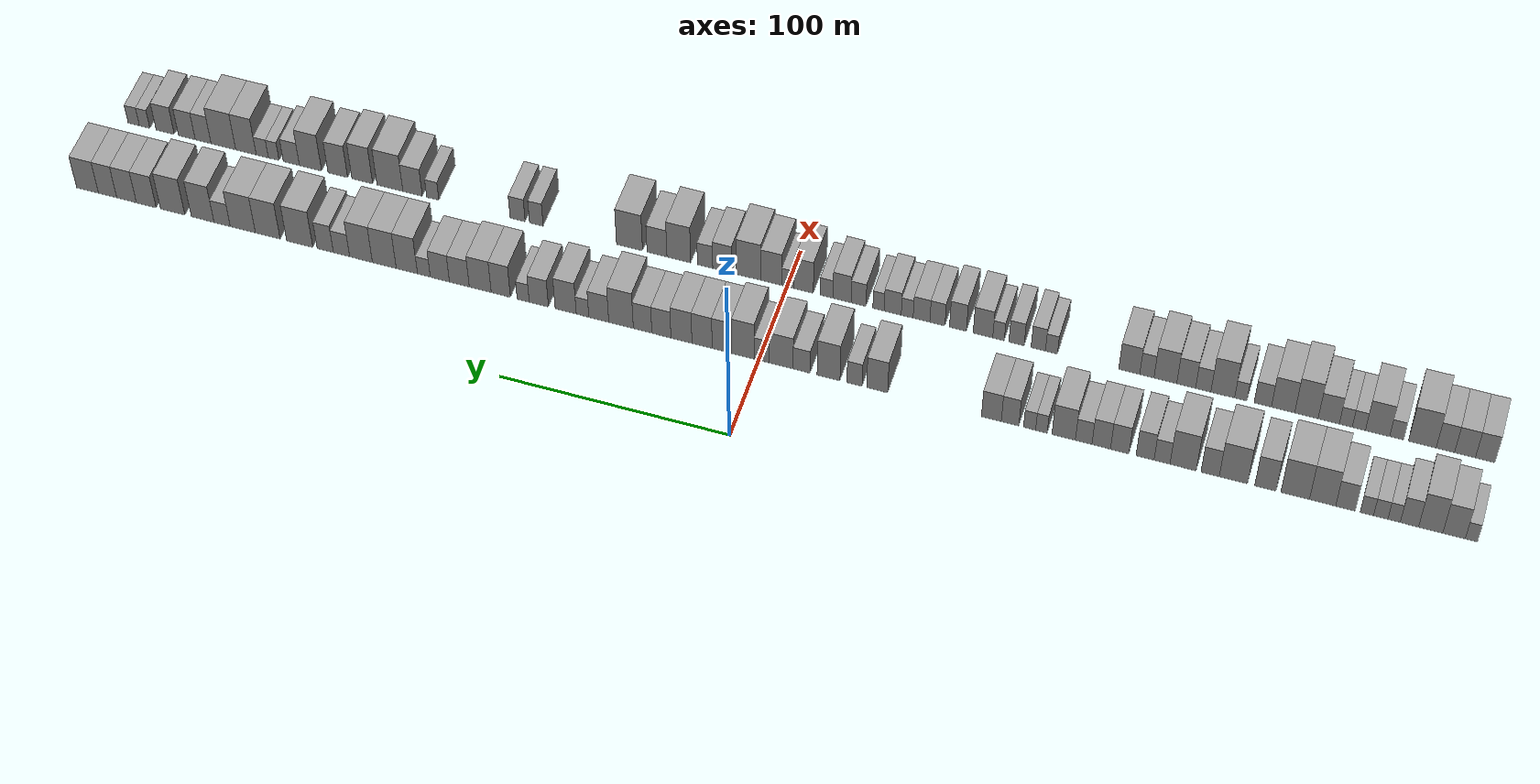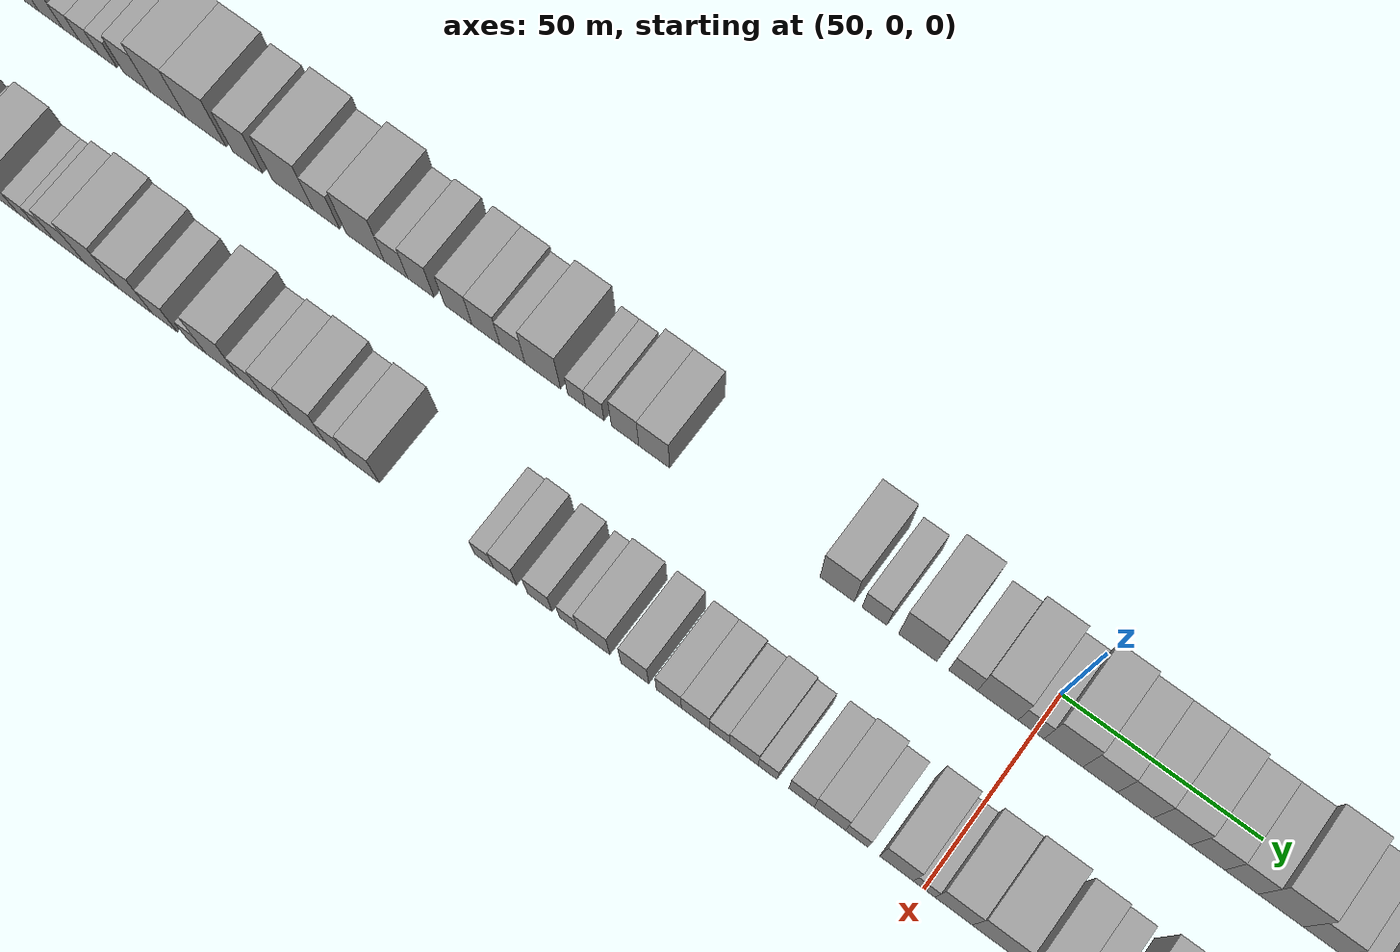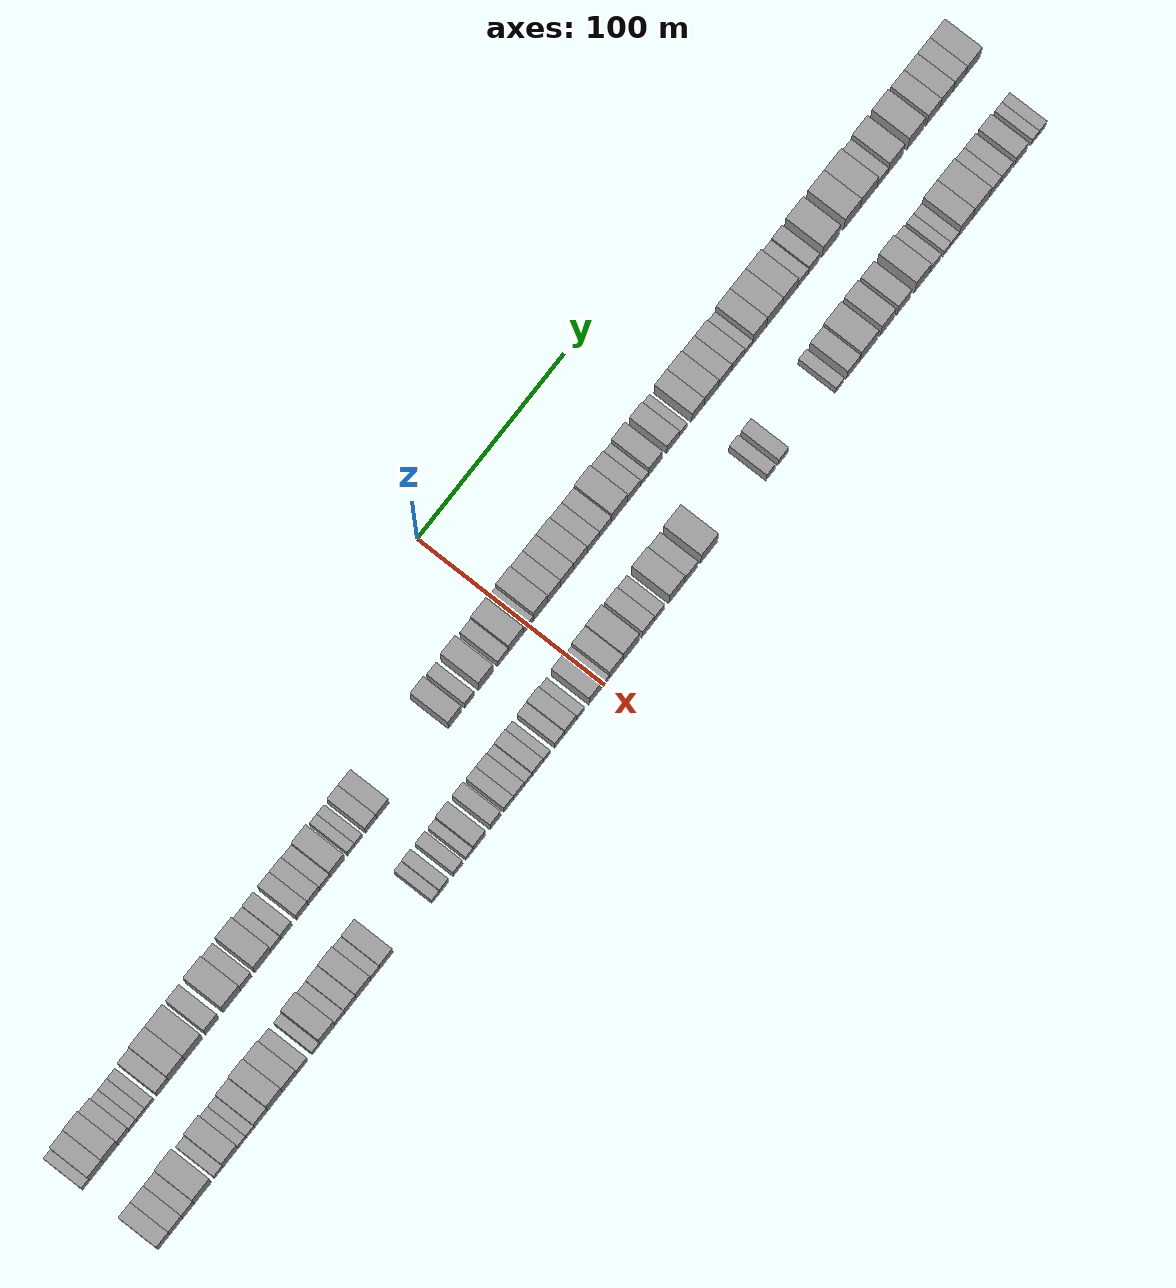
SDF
<sdf version="1.6">
 <world name="default">
  <scene>
   <sky><clouds><speed>12</speed></clouds></sky>
   <ambient>0.4 0.4 0.4 1</ambient>
   <background>0.7 0.7 0.7 1</background>
   <shadows>1</shadows>
  </scene>
  <gravity>0 0 -9.8066</gravity>
  <magnetic_field>6e-06 2.3e-05 -4.2e-05</magnetic_field>
  <physics default="0" name="default_physics" type="ode">
   <ode>
    <solver>
     <type>quick</type>
     <iters>10</iters>
     <sor>1.0</sor>
     <use_dynamic_moi_rescaling>0</use_dynamic_moi_rescaling>
    </solver>
    <constraints>
     <cfm>0</cfm>
     <erp>0.2</erp>
     <contact_max_correcting_vel>100</contact_max_correcting_vel>
     <contact_surface_layer>0.001</contact_surface_layer>
    </constraints>
   </ode>
   <max_step_size>0.004</max_step_size>
   <real_time_factor>1</real_time_factor>
   <real_time_update_rate>250</real_time_update_rate>
  </physics>
  <light name="sun" type="directional">
   <pose>0 0 10 0 0 0</pose>
   <diffuse>0.8 0.8 0.8 1</diffuse>
   <specular>0.2 0.2 0.2 1</specular>
   <attenuation>
    <range>1000</range>
    <constant>0.9</constant>
    <linear>0.01</linear>
    <quadratic>0.001</quadratic>
   </attenuation>
   <direction>-0.5 0.1 -0.9</direction>
  </light>
  <model name="building_1">
   <static>1</static>
   <pose>50.0000 -297.5527 0 0.000000 0.000000 0.000000</pose>
   <link name="link">
    <pose>0 0 6.00 0 0 0</pose>
    <collision name="collision"><geometry><box><size>20.0000 4.8946 12.0000</size></box></geometry></collision>
    <visual name="visual">
     <cast_shadows>0</cast_shadows>
     <geometry><box><size>20.0000 4.8946 12.0000</size></box></geometry>
     <material>
      <script>
       <uri>model://grey_wall/materials/scripts</uri>
       <uri>model://grey_wall/materials/textures</uri>
       <name>vrc/grey_wall</name>
      </script>
     </material>
    </visual>
   </link>
  </model>
  <model name="building_2">
   <static>1</static>
   <pose>50.0000 -290.5710 0 0.000000 0.000000 0.000000</pose>
   <link name="link">
    <pose>0 0 10.50 0 0 0</pose>
    <collision name="collision"><geometry><box><size>20.0000 9.0688 21.0000</size></box></geometry></collision>
    <visual name="visual">
     <cast_shadows>0</cast_shadows>
     <geometry><box><size>20.0000 9.0688 21.0000</size></box></geometry>
     <material>
      <script>
       <uri>model://grey_wall/materials/scripts</uri>
       <uri>model://grey_wall/materials/textures</uri>
       <name>vrc/grey_wall</name>
      </script>
     </material>
    </visual>
   </link>
  </model>
  <model name="building_3">
   <static>1</static>
   <pose>50.0000 -281.1410 0 0.000000 0.000000 0.000000</pose>
   <link name="link">
    <pose>0 0 12.00 0 0 0</pose>
    <collision name="collision"><geometry><box><size>20.0000 9.7911 24.0000</size></box></geometry></collision>
    <visual name="visual">
     <cast_shadows>0</cast_shadows>
     <geometry><box><size>20.0000 9.7911 24.0000</size></box></geometry>
     <material>
      <script>
       <uri>model://grey_wall/materials/scripts</uri>
       <uri>model://grey_wall/materials/textures</uri>
       <name>vrc/grey_wall</name>
      </script>
     </material>
    </visual>
   </link>
  </model>
  <model name="building_4">
   <static>1</static>
   <pose>50.0000 -272.5372 0 0.000000 0.000000 0.000000</pose>
   <link name="link">
    <pose>0 0 9.00 0 0 0</pose>
    <collision name="collision"><geometry><box><size>20.0000 7.4165 18.0000</size></box></geometry></collision>
    <visual name="visual">
     <cast_shadows>0</cast_shadows>
     <geometry><box><size>20.0000 7.4165 18.0000</size></box></geometry>
     <material>
      <script>
       <uri>model://grey_wall/materials/scripts</uri>
       <uri>model://grey_wall/materials/textures</uri>
       <name>vrc/grey_wall</name>
      </script>
     </material>
    </visual>
   </link>
  </model>
  <model name="building_5">
   <static>1</static>
   <pose>50.0000 -266.3257 0 0.000000 0.000000 0.000000</pose>
   <link name="link">
    <pose>0 0 6.00 0 0 0</pose>
    <collision name="collision"><geometry><box><size>20.0000 5.0066 12.0000</size></box></geometry></collision>
    <visual name="visual">
     <cast_shadows>0</cast_shadows>
     <geometry><box><size>20.0000 5.0066 12.0000</size></box></geometry>
     <material>
      <script>
       <uri>model://grey_wall/materials/scripts</uri>
       <uri>model://grey_wall/materials/textures</uri>
       <name>vrc/grey_wall</name>
      </script>
     </material>
    </visual>
   </link>
  </model>
  <model name="building_6">
   <static>1</static>
   <pose>50.0000 -260.9145 0 0.000000 0.000000 0.000000</pose>
   <link name="link">
    <pose>0 0 6.00 0 0 0</pose>
    <collision name="collision"><geometry><box><size>20.0000 5.8157 12.0000</size></box></geometry></collision>
    <visual name="visual">
     <cast_shadows>0</cast_shadows>
     <geometry><box><size>20.0000 5.8157 12.0000</size></box></geometry>
     <material>
      <script>
       <uri>model://grey_wall/materials/scripts</uri>
       <uri>model://grey_wall/materials/textures</uri>
       <name>vrc/grey_wall</name>
      </script>
     </material>
    </visual>
   </link>
  </model>
  <model name="building_7">
   <static>1</static>
   <pose>50.0000 -255.2807 0 0.000000 0.000000 0.000000</pose>
   <link name="link">
    <pose>0 0 6.00 0 0 0</pose>
    <collision name="collision"><geometry><box><size>20.0000 5.4520 12.0000</size></box></geometry></collision>
    <visual name="visual">
     <cast_shadows>0</cast_shadows>
     <geometry><box><size>20.0000 5.4520 12.0000</size></box></geometry>
     <material>
      <script>
       <uri>model://grey_wall/materials/scripts</uri>
       <uri>model://grey_wall/materials/textures</uri>
       <name>vrc/grey_wall</name>
      </script>
     </material>
    </visual>
   </link>
  </model>
  <model name="building_8">
   <static>1</static>
   <pose>50.0000 -246.5573 0 0.000000 0.000000 0.000000</pose>
   <link name="link">
    <pose>0 0 9.00 0 0 0</pose>
    <collision name="collision"><geometry><box><size>20.0000 7.9948 18.0000</size></box></geometry></collision>
    <visual name="visual">
     <cast_shadows>0</cast_shadows>
     <geometry><box><size>20.0000 7.9948 18.0000</size></box></geometry>
     <material>
      <script>
       <uri>model://grey_wall/materials/scripts</uri>
       <uri>model://grey_wall/materials/textures</uri>
       <name>vrc/grey_wall</name>
      </script>
     </material>
    </visual>
   </link>
  </model>
  <model name="building_9">
   <static>1</static>
   <pose>50.0000 -237.2130 0 0.000000 0.000000 0.000000</pose>
   <link name="link">
    <pose>0 0 12.00 0 0 0</pose>
    <collision name="collision"><geometry><box><size>20.0000 10.6939 24.0000</size></box></geometry></collision>
    <visual name="visual">
     <cast_shadows>0</cast_shadows>
     <geometry><box><size>20.0000 10.6939 24.0000</size></box></geometry>
     <material>
      <script>
       <uri>model://grey_wall/materials/scripts</uri>
       <uri>model://grey_wall/materials/textures</uri>
       <name>vrc/grey_wall</name>
      </script>
     </material>
    </visual>
   </link>
  </model>
  <model name="building_10">
   <static>1</static>
   <pose>50.0000 -226.0155 0 0.000000 0.000000 0.000000</pose>
   <link name="link">
    <pose>0 0 12.00 0 0 0</pose>
    <collision name="collision"><geometry><box><size>20.0000 11.7012 24.0000</size></box></geometry></collision>
    <visual name="visual">
     <cast_shadows>0</cast_shadows>
     <geometry><box><size>20.0000 11.7012 24.0000</size></box></geometry>
     <material>
      <script>
       <uri>model://grey_wall/materials/scripts</uri>
       <uri>model://grey_wall/materials/textures</uri>
       <name>vrc/grey_wall</name>
      </script>
     </material>
    </visual>
   </link>
  </model>
  <model name="building_11">
   <static>1</static>
   <pose>50.0000 -213.7931 0 0.000000 0.000000 0.000000</pose>
   <link name="link">
    <pose>0 0 10.50 0 0 0</pose>
    <collision name="collision"><geometry><box><size>20.0000 8.7436 21.0000</size></box></geometry></collision>
    <visual name="visual">
     <cast_shadows>0</cast_shadows>
     <geometry><box><size>20.0000 8.7436 21.0000</size></box></geometry>
     <material>
      <script>
       <uri>model://grey_wall/materials/scripts</uri>
       <uri>model://grey_wall/materials/textures</uri>
       <name>vrc/grey_wall</name>
      </script>
     </material>
    </visual>
   </link>
  </model>
  <model name="building_12">
   <static>1</static>
   <pose>50.0000 -200.5853 0 0.000000 0.000000 0.000000</pose>
   <link name="link">
    <pose>0 0 12.00 0 0 0</pose>
    <collision name="collision"><geometry><box><size>20.0000 11.6719 24.0000</size></box></geometry></collision>
    <visual name="visual">
     <cast_shadows>0</cast_shadows>
     <geometry><box><size>20.0000 11.6719 24.0000</size></box></geometry>
     <material>
      <script>
       <uri>model://grey_wall/materials/scripts</uri>
       <uri>model://grey_wall/materials/textures</uri>
       <name>vrc/grey_wall</name>
      </script>
     </material>
    </visual>
   </link>
  </model>
  <model name="building_13">
   <static>1</static>
   <pose>50.0000 -190.9823 0 0.000000 0.000000 0.000000</pose>
   <link name="link">
    <pose>0 0 9.00 0 0 0</pose>
    <collision name="collision"><geometry><box><size>20.0000 7.5342 18.0000</size></box></geometry></collision>
    <visual name="visual">
     <cast_shadows>0</cast_shadows>
     <geometry><box><size>20.0000 7.5342 18.0000</size></box></geometry>
     <material>
      <script>
       <uri>model://grey_wall/materials/scripts</uri>
       <uri>model://grey_wall/materials/textures</uri>
       <name>vrc/grey_wall</name>
      </script>
     </material>
    </visual>
   </link>
  </model>
  <model name="building_14">
   <static>1</static>
   <pose>50.0000 -179.7867 0 0.000000 0.000000 0.000000</pose>
   <link name="link">
    <pose>0 0 12.00 0 0 0</pose>
    <collision name="collision"><geometry><box><size>20.0000 10.8569 24.0000</size></box></geometry></collision>
    <visual name="visual">
     <cast_shadows>0</cast_shadows>
     <geometry><box><size>20.0000 10.8569 24.0000</size></box></geometry>
     <material>
      <script>
       <uri>model://grey_wall/materials/scripts</uri>
       <uri>model://grey_wall/materials/textures</uri>
       <name>vrc/grey_wall</name>
      </script>
     </material>
    </visual>
   </link>
  </model>
  <model name="building_15">
   <static>1</static>
   <pose>50.0000 -171.0333 0 0.000000 0.000000 0.000000</pose>
   <link name="link">
    <pose>0 0 7.50 0 0 0</pose>
    <collision name="collision"><geometry><box><size>20.0000 6.6499 15.0000</size></box></geometry></collision>
    <visual name="visual">
     <cast_shadows>0</cast_shadows>
     <geometry><box><size>20.0000 6.6499 15.0000</size></box></geometry>
     <material>
      <script>
       <uri>model://grey_wall/materials/scripts</uri>
       <uri>model://grey_wall/materials/textures</uri>
       <name>vrc/grey_wall</name>
      </script>
     </material>
    </visual>
   </link>
  </model>
  <model name="building_16">
   <static>1</static>
   <pose>50.0000 -163.9777 0 0.000000 0.000000 0.000000</pose>
   <link name="link">
    <pose>0 0 9.00 0 0 0</pose>
    <collision name="collision"><geometry><box><size>20.0000 7.4614 18.0000</size></box></geometry></collision>
    <visual name="visual">
     <cast_shadows>0</cast_shadows>
     <geometry><box><size>20.0000 7.4614 18.0000</size></box></geometry>
     <material>
      <script>
       <uri>model://grey_wall/materials/scripts</uri>
       <uri>model://grey_wall/materials/textures</uri>
       <name>vrc/grey_wall</name>
      </script>
     </material>
    </visual>
   </link>
  </model>
  <model name="building_17">
   <static>1</static>
   <pose>50.0000 -153.3974 0 0.000000 0.000000 0.000000</pose>
   <link name="link">
    <pose>0 0 9.00 0 0 0</pose>
    <collision name="collision"><geometry><box><size>20.0000 7.6990 18.0000</size></box></geometry></collision>
    <visual name="visual">
     <cast_shadows>0</cast_shadows>
     <geometry><box><size>20.0000 7.6990 18.0000</size></box></geometry>
     <material>
      <script>
       <uri>model://grey_wall/materials/scripts</uri>
       <uri>model://grey_wall/materials/textures</uri>
       <name>vrc/grey_wall</name>
      </script>
     </material>
    </visual>
   </link>
  </model>
  <model name="building_18">
   <static>1</static>
   <pose>50.0000 -145.6617 0 0.000000 0.000000 0.000000</pose>
   <link name="link">
    <pose>0 0 9.00 0 0 0</pose>
    <collision name="collision"><geometry><box><size>20.0000 7.7725 18.0000</size></box></geometry></collision>
    <visual name="visual">
     <cast_shadows>0</cast_shadows>
     <geometry><box><size>20.0000 7.7725 18.0000</size></box></geometry>
     <material>
      <script>
       <uri>model://grey_wall/materials/scripts</uri>
       <uri>model://grey_wall/materials/textures</uri>
       <name>vrc/grey_wall</name>
      </script>
     </material>
    </visual>
   </link>
  </model>
  <model name="building_19">
   <static>1</static>
   <pose>50.0000 -138.2961 0 0.000000 0.000000 0.000000</pose>
   <link name="link">
    <pose>0 0 7.50 0 0 0</pose>
    <collision name="collision"><geometry><box><size>20.0000 6.9588 15.0000</size></box></geometry></collision>
    <visual name="visual">
     <cast_shadows>0</cast_shadows>
     <geometry><box><size>20.0000 6.9588 15.0000</size></box></geometry>
     <material>
      <script>
       <uri>model://grey_wall/materials/scripts</uri>
       <uri>model://grey_wall/materials/textures</uri>
       <name>vrc/grey_wall</name>
      </script>
     </material>
    </visual>
   </link>
  </model>
  <model name="building_20">
   <static>1</static>
   <pose>50.0000 -129.9064 0 0.000000 0.000000 0.000000</pose>
   <link name="link">
    <pose>0 0 10.50 0 0 0</pose>
    <collision name="collision"><geometry><box><size>20.0000 9.8205 21.0000</size></box></geometry></collision>
    <visual name="visual">
     <cast_shadows>0</cast_shadows>
     <geometry><box><size>20.0000 9.8205 21.0000</size></box></geometry>
     <material>
      <script>
       <uri>model://grey_wall/materials/scripts</uri>
       <uri>model://grey_wall/materials/textures</uri>
       <name>vrc/grey_wall</name>
      </script>
     </material>
    </visual>
   </link>
  </model>
  <model name="building_21">
   <static>1</static>
   <pose>50.0000 -120.5485 0 0.000000 0.000000 0.000000</pose>
   <link name="link">
    <pose>0 0 6.00 0 0 0</pose>
    <collision name="collision"><geometry><box><size>20.0000 4.8953 12.0000</size></box></geometry></collision>
    <visual name="visual">
     <cast_shadows>0</cast_shadows>
     <geometry><box><size>20.0000 4.8953 12.0000</size></box></geometry>
     <material>
      <script>
       <uri>model://grey_wall/materials/scripts</uri>
       <uri>model://grey_wall/materials/textures</uri>
       <name>vrc/grey_wall</name>
      </script>
     </material>
    </visual>
   </link>
  </model>
  <model name="building_22">
   <static>1</static>
   <pose>50.0000 -115.5680 0 0.000000 0.000000 0.000000</pose>
   <link name="link">
    <pose>0 0 6.00 0 0 0</pose>
    <collision name="collision"><geometry><box><size>20.0000 5.0657 12.0000</size></box></geometry></collision>
    <visual name="visual">
     <cast_shadows>0</cast_shadows>
     <geometry><box><size>20.0000 5.0657 12.0000</size></box></geometry>
     <material>
      <script>
       <uri>model://grey_wall/materials/scripts</uri>
       <uri>model://grey_wall/materials/textures</uri>
       <name>vrc/grey_wall</name>
      </script>
     </material>
    </visual>
   </link>
  </model>
  <model name="building_23">
   <static>1</static>
   <pose>50.0000 -107.3214 0 0.000000 0.000000 0.000000</pose>
   <link name="link">
    <pose>0 0 9.00 0 0 0</pose>
    <collision name="collision"><geometry><box><size>20.0000 7.4274 18.0000</size></box></geometry></collision>
    <visual name="visual">
     <cast_shadows>0</cast_shadows>
     <geometry><box><size>20.0000 7.4274 18.0000</size></box></geometry>
     <material>
      <script>
       <uri>model://grey_wall/materials/scripts</uri>
       <uri>model://grey_wall/materials/textures</uri>
       <name>vrc/grey_wall</name>
      </script>
     </material>
    </visual>
   </link>
  </model>
  <model name="building_24">
   <static>1</static>
   <pose>50.0000 -99.4239 0 0.000000 0.000000 0.000000</pose>
   <link name="link">
    <pose>0 0 9.00 0 0 0</pose>
    <collision name="collision"><geometry><box><size>20.0000 8.3677 18.0000</size></box></geometry></collision>
    <visual name="visual">
     <cast_shadows>0</cast_shadows>
     <geometry><box><size>20.0000 8.3677 18.0000</size></box></geometry>
     <material>
      <script>
       <uri>model://grey_wall/materials/scripts</uri>
       <uri>model://grey_wall/materials/textures</uri>
       <name>vrc/grey_wall</name>
      </script>
     </material>
    </visual>
   </link>
  </model>
  <model name="building_25">
   <static>1</static>
   <pose>50.0000 -50.7242 0 0.000000 0.000000 0.000000</pose>
   <link name="link">
    <pose>0 0 10.50 0 0 0</pose>
    <collision name="collision"><geometry><box><size>20.0000 9.0105 21.0000</size></box></geometry></collision>
    <visual name="visual">
     <cast_shadows>0</cast_shadows>
     <geometry><box><size>20.0000 9.0105 21.0000</size></box></geometry>
     <material>
      <script>
       <uri>model://grey_wall/materials/scripts</uri>
       <uri>model://grey_wall/materials/textures</uri>
       <name>vrc/grey_wall</name>
      </script>
     </material>
    </visual>
   </link>
  </model>
  <model name="building_26">
   <static>1</static>
   <pose>50.0000 -40.9779 0 0.000000 0.000000 0.000000</pose>
   <link name="link">
    <pose>0 0 7.50 0 0 0</pose>
    <collision name="collision"><geometry><box><size>20.0000 6.4822 15.0000</size></box></geometry></collision>
    <visual name="visual">
     <cast_shadows>0</cast_shadows>
     <geometry><box><size>20.0000 6.4822 15.0000</size></box></geometry>
     <material>
      <script>
       <uri>model://grey_wall/materials/scripts</uri>
       <uri>model://grey_wall/materials/textures</uri>
       <name>vrc/grey_wall</name>
      </script>
     </material>
    </visual>
   </link>
  </model>
  <model name="building_27">
   <static>1</static>
   <pose>50.0000 -29.8061 0 0.000000 0.000000 0.000000</pose>
   <link name="link">
    <pose>0 0 12.00 0 0 0</pose>
    <collision name="collision"><geometry><box><size>20.0000 9.8613 24.0000</size></box></geometry></collision>
    <visual name="visual">
     <cast_shadows>0</cast_shadows>
     <geometry><box><size>20.0000 9.8613 24.0000</size></box></geometry>
     <material>
      <script>
       <uri>model://grey_wall/materials/scripts</uri>
       <uri>model://grey_wall/materials/textures</uri>
       <name>vrc/grey_wall</name>
      </script>
     </material>
    </visual>
   </link>
  </model>
  <model name="building_28">
   <static>1</static>
   <pose>50.0000 -18.1943 0 0.000000 0.000000 0.000000</pose>
   <link name="link">
    <pose>0 0 7.50 0 0 0</pose>
    <collision name="collision"><geometry><box><size>20.0000 7.3623 15.0000</size></box></geometry></collision>
    <visual name="visual">
     <cast_shadows>0</cast_shadows>
     <geometry><box><size>20.0000 7.3623 15.0000</size></box></geometry>
     <material>
      <script>
       <uri>model://grey_wall/materials/scripts</uri>
       <uri>model://grey_wall/materials/textures</uri>
       <name>vrc/grey_wall</name>
      </script>
     </material>
    </visual>
   </link>
  </model>
  <model name="building_29">
   <static>1</static>
   <pose>50.0000 -9.3427 0 0.000000 0.000000 0.000000</pose>
   <link name="link">
    <pose>0 0 10.50 0 0 0</pose>
    <collision name="collision"><geometry><box><size>20.0000 10.3411 21.0000</size></box></geometry></collision>
    <visual name="visual">
     <cast_shadows>0</cast_shadows>
     <geometry><box><size>20.0000 10.3411 21.0000</size></box></geometry>
     <material>
      <script>
       <uri>model://grey_wall/materials/scripts</uri>
       <uri>model://grey_wall/materials/textures</uri>
       <name>vrc/grey_wall</name>
      </script>
     </material>
    </visual>
   </link>
  </model>
  <model name="building_30">
   <static>1</static>
   <pose>50.0000 -0.9263 0 0.000000 0.000000 0.000000</pose>
   <link name="link">
    <pose>0 0 7.50 0 0 0</pose>
    <collision name="collision"><geometry><box><size>20.0000 6.4915 15.0000</size></box></geometry></collision>
    <visual name="visual">
     <cast_shadows>0</cast_shadows>
     <geometry><box><size>20.0000 6.4915 15.0000</size></box></geometry>
     <material>
      <script>
       <uri>model://grey_wall/materials/scripts</uri>
       <uri>model://grey_wall/materials/textures</uri>
       <name>vrc/grey_wall</name>
      </script>
     </material>
    </visual>
   </link>
  </model>
  <model name="building_31">
   <static>1</static>
   <pose>50.0000 7.2069 0 0.000000 0.000000 0.000000</pose>
   <link name="link">
    <pose>0 0 12.00 0 0 0</pose>
    <collision name="collision"><geometry><box><size>20.0000 9.7750 24.0000</size></box></geometry></collision>
    <visual name="visual">
     <cast_shadows>0</cast_shadows>
     <geometry><box><size>20.0000 9.7750 24.0000</size></box></geometry>
     <material>
      <script>
       <uri>model://grey_wall/materials/scripts</uri>
       <uri>model://grey_wall/materials/textures</uri>
       <name>vrc/grey_wall</name>
      </script>
     </material>
    </visual>
   </link>
  </model>
  <model name="building_32">
   <static>1</static>
   <pose>50.0000 16.3953 0 0.000000 0.000000 0.000000</pose>
   <link name="link">
    <pose>0 0 10.50 0 0 0</pose>
    <collision name="collision"><geometry><box><size>20.0000 8.6017 21.0000</size></box></geometry></collision>
    <visual name="visual">
     <cast_shadows>0</cast_shadows>
     <geometry><box><size>20.0000 8.6017 21.0000</size></box></geometry>
     <material>
      <script>
       <uri>model://grey_wall/materials/scripts</uri>
       <uri>model://grey_wall/materials/textures</uri>
       <name>vrc/grey_wall</name>
      </script>
     </material>
    </visual>
   </link>
  </model>
  <model name="building_33">
   <static>1</static>
   <pose>50.0000 25.1196 0 0.000000 0.000000 0.000000</pose>
   <link name="link">
    <pose>0 0 10.50 0 0 0</pose>
    <collision name="collision"><geometry><box><size>20.0000 8.8470 21.0000</size></box></geometry></collision>
    <visual name="visual">
     <cast_shadows>0</cast_shadows>
     <geometry><box><size>20.0000 8.8470 21.0000</size></box></geometry>
     <material>
      <script>
       <uri>model://grey_wall/materials/scripts</uri>
       <uri>model://grey_wall/materials/textures</uri>
       <name>vrc/grey_wall</name>
      </script>
     </material>
    </visual>
   </link>
  </model>
  <model name="building_34">
   <static>1</static>
   <pose>50.0000 34.1502 0 0.000000 0.000000 0.000000</pose>
   <link name="link">
    <pose>0 0 10.50 0 0 0</pose>
    <collision name="collision"><geometry><box><size>20.0000 9.2142 21.0000</size></box></geometry></collision>
    <visual name="visual">
     <cast_shadows>0</cast_shadows>
     <geometry><box><size>20.0000 9.2142 21.0000</size></box></geometry>
     <material>
      <script>
       <uri>model://grey_wall/materials/scripts</uri>
       <uri>model://grey_wall/materials/textures</uri>
       <name>vrc/grey_wall</name>
      </script>
     </material>
    </visual>
   </link>
  </model>
  <model name="building_35">
   <static>1</static>
   <pose>50.0000 42.9496 0 0.000000 0.000000 0.000000</pose>
   <link name="link">
    <pose>0 0 9.00 0 0 0</pose>
    <collision name="collision"><geometry><box><size>20.0000 8.3844 18.0000</size></box></geometry></collision>
    <visual name="visual">
     <cast_shadows>0</cast_shadows>
     <geometry><box><size>20.0000 8.3844 18.0000</size></box></geometry>
     <material>
      <script>
       <uri>model://grey_wall/materials/scripts</uri>
       <uri>model://grey_wall/materials/textures</uri>
       <name>vrc/grey_wall</name>
      </script>
     </material>
    </visual>
   </link>
  </model>
  <model name="building_36">
   <static>1</static>
   <pose>50.0000 51.2232 0 0.000000 0.000000 0.000000</pose>
   <link name="link">
    <pose>0 0 9.00 0 0 0</pose>
    <collision name="collision"><geometry><box><size>20.0000 8.1629 18.0000</size></box></geometry></collision>
    <visual name="visual">
     <cast_shadows>0</cast_shadows>
     <geometry><box><size>20.0000 8.1629 18.0000</size></box></geometry>
     <material>
      <script>
       <uri>model://grey_wall/materials/scripts</uri>
       <uri>model://grey_wall/materials/textures</uri>
       <name>vrc/grey_wall</name>
      </script>
     </material>
    </visual>
   </link>
  </model>
  <model name="building_37">
   <static>1</static>
   <pose>50.0000 60.7332 0 0.000000 0.000000 0.000000</pose>
   <link name="link">
    <pose>0 0 12.00 0 0 0</pose>
    <collision name="collision"><geometry><box><size>20.0000 10.8570 24.0000</size></box></geometry></collision>
    <visual name="visual">
     <cast_shadows>0</cast_shadows>
     <geometry><box><size>20.0000 10.8570 24.0000</size></box></geometry>
     <material>
      <script>
       <uri>model://grey_wall/materials/scripts</uri>
       <uri>model://grey_wall/materials/textures</uri>
       <name>vrc/grey_wall</name>
      </script>
     </material>
    </visual>
   </link>
  </model>
  <model name="building_38">
   <static>1</static>
   <pose>50.0000 70.5709 0 0.000000 0.000000 0.000000</pose>
   <link name="link">
    <pose>0 0 9.00 0 0 0</pose>
    <collision name="collision"><geometry><box><size>20.0000 8.8184 18.0000</size></box></geometry></collision>
    <visual name="visual">
     <cast_shadows>0</cast_shadows>
     <geometry><box><size>20.0000 8.8184 18.0000</size></box></geometry>
     <material>
      <script>
       <uri>model://grey_wall/materials/scripts</uri>
       <uri>model://grey_wall/materials/textures</uri>
       <name>vrc/grey_wall</name>
      </script>
     </material>
    </visual>
   </link>
  </model>
  <model name="building_39">
   <static>1</static>
   <pose>50.0000 77.7623 0 0.000000 0.000000 0.000000</pose>
   <link name="link">
    <pose>0 0 6.00 0 0 0</pose>
    <collision name="collision"><geometry><box><size>20.0000 5.5645 12.0000</size></box></geometry></collision>
    <visual name="visual">
     <cast_shadows>0</cast_shadows>
     <geometry><box><size>20.0000 5.5645 12.0000</size></box></geometry>
     <material>
      <script>
       <uri>model://grey_wall/materials/scripts</uri>
       <uri>model://grey_wall/materials/textures</uri>
       <name>vrc/grey_wall</name>
      </script>
     </material>
    </visual>
   </link>
  </model>
  <model name="building_40">
   <static>1</static>
   <pose>50.0000 85.2182 0 0.000000 0.000000 0.000000</pose>
   <link name="link">
    <pose>0 0 10.50 0 0 0</pose>
    <collision name="collision"><geometry><box><size>20.0000 9.3475 21.0000</size></box></geometry></collision>
    <visual name="visual">
     <cast_shadows>0</cast_shadows>
     <geometry><box><size>20.0000 9.3475 21.0000</size></box></geometry>
     <material>
      <script>
       <uri>model://grey_wall/materials/scripts</uri>
       <uri>model://grey_wall/materials/textures</uri>
       <name>vrc/grey_wall</name>
      </script>
     </material>
    </visual>
   </link>
  </model>
  <model name="building_41">
   <static>1</static>
   <pose>50.0000 97.1692 0 0.000000 0.000000 0.000000</pose>
   <link name="link">
    <pose>0 0 9.00 0 0 0</pose>
    <collision name="collision"><geometry><box><size>20.0000 8.5545 18.0000</size></box></geometry></collision>
    <visual name="visual">
     <cast_shadows>0</cast_shadows>
     <geometry><box><size>20.0000 8.5545 18.0000</size></box></geometry>
     <material>
      <script>
       <uri>model://grey_wall/materials/scripts</uri>
       <uri>model://grey_wall/materials/textures</uri>
       <name>vrc/grey_wall</name>
      </script>
     </material>
    </visual>
   </link>
  </model>
  <model name="building_42">
   <static>1</static>
   <pose>50.0000 104.1438 0 0.000000 0.000000 0.000000</pose>
   <link name="link">
    <pose>0 0 6.00 0 0 0</pose>
    <collision name="collision"><geometry><box><size>20.0000 5.3945 12.0000</size></box></geometry></collision>
    <visual name="visual">
     <cast_shadows>0</cast_shadows>
     <geometry><box><size>20.0000 5.3945 12.0000</size></box></geometry>
     <material>
      <script>
       <uri>model://grey_wall/materials/scripts</uri>
       <uri>model://grey_wall/materials/textures</uri>
       <name>vrc/grey_wall</name>
      </script>
     </material>
    </visual>
   </link>
  </model>
  <model name="building_43">
   <static>1</static>
   <pose>50.0000 114.1314 0 0.000000 0.000000 0.000000</pose>
   <link name="link">
    <pose>0 0 10.50 0 0 0</pose>
    <collision name="collision"><geometry><box><size>20.0000 8.5808 21.0000</size></box></geometry></collision>
    <visual name="visual">
     <cast_shadows>0</cast_shadows>
     <geometry><box><size>20.0000 8.5808 21.0000</size></box></geometry>
     <material>
      <script>
       <uri>model://grey_wall/materials/scripts</uri>
       <uri>model://grey_wall/materials/textures</uri>
       <name>vrc/grey_wall</name>
      </script>
     </material>
    </visual>
   </link>
  </model>
  <model name="building_44">
   <static>1</static>
   <pose>50.0000 123.3507 0 0.000000 0.000000 0.000000</pose>
   <link name="link">
    <pose>0 0 10.50 0 0 0</pose>
    <collision name="collision"><geometry><box><size>20.0000 9.8578 21.0000</size></box></geometry></collision>
    <visual name="visual">
     <cast_shadows>0</cast_shadows>
     <geometry><box><size>20.0000 9.8578 21.0000</size></box></geometry>
     <material>
      <script>
       <uri>model://grey_wall/materials/scripts</uri>
       <uri>model://grey_wall/materials/textures</uri>
       <name>vrc/grey_wall</name>
      </script>
     </material>
    </visual>
   </link>
  </model>
  <model name="building_45">
   <static>1</static>
   <pose>50.0000 132.7346 0 0.000000 0.000000 0.000000</pose>
   <link name="link">
    <pose>0 0 9.00 0 0 0</pose>
    <collision name="collision"><geometry><box><size>20.0000 8.9099 18.0000</size></box></geometry></collision>
    <visual name="visual">
     <cast_shadows>0</cast_shadows>
     <geometry><box><size>20.0000 8.9099 18.0000</size></box></geometry>
     <material>
      <script>
       <uri>model://grey_wall/materials/scripts</uri>
       <uri>model://grey_wall/materials/textures</uri>
       <name>vrc/grey_wall</name>
      </script>
     </material>
    </visual>
   </link>
  </model>
  <model name="building_46">
   <static>1</static>
   <pose>50.0000 141.5011 0 0.000000 0.000000 0.000000</pose>
   <link name="link">
    <pose>0 0 9.00 0 0 0</pose>
    <collision name="collision"><geometry><box><size>20.0000 8.6232 18.0000</size></box></geometry></collision>
    <visual name="visual">
     <cast_shadows>0</cast_shadows>
     <geometry><box><size>20.0000 8.6232 18.0000</size></box></geometry>
     <material>
      <script>
       <uri>model://grey_wall/materials/scripts</uri>
       <uri>model://grey_wall/materials/textures</uri>
       <name>vrc/grey_wall</name>
      </script>
     </material>
    </visual>
   </link>
  </model>
  <model name="building_47">
   <static>1</static>
   <pose>50.0000 148.7037 0 0.000000 0.000000 0.000000</pose>
   <link name="link">
    <pose>0 0 6.00 0 0 0</pose>
    <collision name="collision"><geometry><box><size>20.0000 5.7819 12.0000</size></box></geometry></collision>
    <visual name="visual">
     <cast_shadows>0</cast_shadows>
     <geometry><box><size>20.0000 5.7819 12.0000</size></box></geometry>
     <material>
      <script>
       <uri>model://grey_wall/materials/scripts</uri>
       <uri>model://grey_wall/materials/textures</uri>
       <name>vrc/grey_wall</name>
      </script>
     </material>
    </visual>
   </link>
  </model>
  <model name="building_48">
   <static>1</static>
   <pose>50.0000 156.4037 0 0.000000 0.000000 0.000000</pose>
   <link name="link">
    <pose>0 0 12.00 0 0 0</pose>
    <collision name="collision"><geometry><box><size>20.0000 9.6182 24.0000</size></box></geometry></collision>
    <visual name="visual">
     <cast_shadows>0</cast_shadows>
     <geometry><box><size>20.0000 9.6182 24.0000</size></box></geometry>
     <material>
      <script>
       <uri>model://grey_wall/materials/scripts</uri>
       <uri>model://grey_wall/materials/textures</uri>
       <name>vrc/grey_wall</name>
      </script>
     </material>
    </visual>
   </link>
  </model>
  <model name="building_49">
   <static>1</static>
   <pose>50.0000 166.6151 0 0.000000 0.000000 0.000000</pose>
   <link name="link">
    <pose>0 0 12.00 0 0 0</pose>
    <collision name="collision"><geometry><box><size>20.0000 10.8045 24.0000</size></box></geometry></collision>
    <visual name="visual">
     <cast_shadows>0</cast_shadows>
     <geometry><box><size>20.0000 10.8045 24.0000</size></box></geometry>
     <material>
      <script>
       <uri>model://grey_wall/materials/scripts</uri>
       <uri>model://grey_wall/materials/textures</uri>
       <name>vrc/grey_wall</name>
      </script>
     </material>
    </visual>
   </link>
  </model>
  <model name="building_50">
   <static>1</static>
   <pose>50.0000 177.2005 0 0.000000 0.000000 0.000000</pose>
   <link name="link">
    <pose>0 0 12.00 0 0 0</pose>
    <collision name="collision"><geometry><box><size>20.0000 10.3664 24.0000</size></box></geometry></collision>
    <visual name="visual">
     <cast_shadows>0</cast_shadows>
     <geometry><box><size>20.0000 10.3664 24.0000</size></box></geometry>
     <material>
      <script>
       <uri>model://grey_wall/materials/scripts</uri>
       <uri>model://grey_wall/materials/textures</uri>
       <name>vrc/grey_wall</name>
      </script>
     </material>
    </visual>
   </link>
  </model>
  <model name="building_51">
   <static>1</static>
   <pose>50.0000 186.0834 0 0.000000 0.000000 0.000000</pose>
   <link name="link">
    <pose>0 0 7.50 0 0 0</pose>
    <collision name="collision"><geometry><box><size>20.0000 7.3994 15.0000</size></box></geometry></collision>
    <visual name="visual">
     <cast_shadows>0</cast_shadows>
     <geometry><box><size>20.0000 7.3994 15.0000</size></box></geometry>
     <material>
      <script>
       <uri>model://grey_wall/materials/scripts</uri>
       <uri>model://grey_wall/materials/textures</uri>
       <name>vrc/grey_wall</name>
      </script>
     </material>
    </visual>
   </link>
  </model>
  <model name="building_52">
   <static>1</static>
   <pose>50.0000 193.4686 0 0.000000 0.000000 0.000000</pose>
   <link name="link">
    <pose>0 0 9.00 0 0 0</pose>
    <collision name="collision"><geometry><box><size>20.0000 7.3710 18.0000</size></box></geometry></collision>
    <visual name="visual">
     <cast_shadows>0</cast_shadows>
     <geometry><box><size>20.0000 7.3710 18.0000</size></box></geometry>
     <material>
      <script>
       <uri>model://grey_wall/materials/scripts</uri>
       <uri>model://grey_wall/materials/textures</uri>
       <name>vrc/grey_wall</name>
      </script>
     </material>
    </visual>
   </link>
  </model>
  <model name="building_53">
   <static>1</static>
   <pose>50.0000 205.1435 0 0.000000 0.000000 0.000000</pose>
   <link name="link">
    <pose>0 0 12.00 0 0 0</pose>
    <collision name="collision"><geometry><box><size>20.0000 11.9788 24.0000</size></box></geometry></collision>
    <visual name="visual">
     <cast_shadows>0</cast_shadows>
     <geometry><box><size>20.0000 11.9788 24.0000</size></box></geometry>
     <material>
      <script>
       <uri>model://grey_wall/materials/scripts</uri>
       <uri>model://grey_wall/materials/textures</uri>
       <name>vrc/grey_wall</name>
      </script>
     </material>
    </visual>
   </link>
  </model>
  <model name="building_54">
   <static>1</static>
   <pose>50.0000 219.8021 0 0.000000 0.000000 0.000000</pose>
   <link name="link">
    <pose>0 0 12.00 0 0 0</pose>
    <collision name="collision"><geometry><box><size>20.0000 11.3384 24.0000</size></box></geometry></collision>
    <visual name="visual">
     <cast_shadows>0</cast_shadows>
     <geometry><box><size>20.0000 11.3384 24.0000</size></box></geometry>
     <material>
      <script>
       <uri>model://grey_wall/materials/scripts</uri>
       <uri>model://grey_wall/materials/textures</uri>
       <name>vrc/grey_wall</name>
      </script>
     </material>
    </visual>
   </link>
  </model>
  <model name="building_55">
   <static>1</static>
   <pose>50.0000 231.2927 0 0.000000 0.000000 0.000000</pose>
   <link name="link">
    <pose>0 0 12.00 0 0 0</pose>
    <collision name="collision"><geometry><box><size>20.0000 11.6429 24.0000</size></box></geometry></collision>
    <visual name="visual">
     <cast_shadows>0</cast_shadows>
     <geometry><box><size>20.0000 11.6429 24.0000</size></box></geometry>
     <material>
      <script>
       <uri>model://grey_wall/materials/scripts</uri>
       <uri>model://grey_wall/materials/textures</uri>
       <name>vrc/grey_wall</name>
      </script>
     </material>
    </visual>
   </link>
  </model>
  <model name="building_56">
   <static>1</static>
   <pose>50.0000 240.8480 0 0.000000 0.000000 0.000000</pose>
   <link name="link">
    <pose>0 0 7.50 0 0 0</pose>
    <collision name="collision"><geometry><box><size>20.0000 7.4675 15.0000</size></box></geometry></collision>
    <visual name="visual">
     <cast_shadows>0</cast_shadows>
     <geometry><box><size>20.0000 7.4675 15.0000</size></box></geometry>
     <material>
      <script>
       <uri>model://grey_wall/materials/scripts</uri>
       <uri>model://grey_wall/materials/textures</uri>
       <name>vrc/grey_wall</name>
      </script>
     </material>
    </visual>
   </link>
  </model>
  <model name="building_57">
   <static>1</static>
   <pose>50.0000 249.8344 0 0.000000 0.000000 0.000000</pose>
   <link name="link">
    <pose>0 0 12.00 0 0 0</pose>
    <collision name="collision"><geometry><box><size>20.0000 10.5054 24.0000</size></box></geometry></collision>
    <visual name="visual">
     <cast_shadows>0</cast_shadows>
     <geometry><box><size>20.0000 10.5054 24.0000</size></box></geometry>
     <material>
      <script>
       <uri>model://grey_wall/materials/scripts</uri>
       <uri>model://grey_wall/materials/textures</uri>
       <name>vrc/grey_wall</name>
      </script>
     </material>
    </visual>
   </link>
  </model>
  <model name="building_58">
   <static>1</static>
   <pose>50.0000 263.7478 0 0.000000 0.000000 0.000000</pose>
   <link name="link">
    <pose>0 0 12.00 0 0 0</pose>
    <collision name="collision"><geometry><box><size>20.0000 11.3214 24.0000</size></box></geometry></collision>
    <visual name="visual">
     <cast_shadows>0</cast_shadows>
     <geometry><box><size>20.0000 11.3214 24.0000</size></box></geometry>
     <material>
      <script>
       <uri>model://grey_wall/materials/scripts</uri>
       <uri>model://grey_wall/materials/textures</uri>
       <name>vrc/grey_wall</name>
      </script>
     </material>
    </visual>
   </link>
  </model>
  <model name="building_59">
   <static>1</static>
   <pose>50.0000 276.0227 0 0.000000 0.000000 0.000000</pose>
   <link name="link">
    <pose>0 0 10.50 0 0 0</pose>
    <collision name="collision"><geometry><box><size>20.0000 9.2283 21.0000</size></box></geometry></collision>
    <visual name="visual">
     <cast_shadows>0</cast_shadows>
     <geometry><box><size>20.0000 9.2283 21.0000</size></box></geometry>
     <material>
      <script>
       <uri>model://grey_wall/materials/scripts</uri>
       <uri>model://grey_wall/materials/textures</uri>
       <name>vrc/grey_wall</name>
      </script>
     </material>
    </visual>
   </link>
  </model>
  <model name="building_60">
   <static>1</static>
   <pose>50.0000 285.2023 0 0.000000 0.000000 0.000000</pose>
   <link name="link">
    <pose>0 0 10.50 0 0 0</pose>
    <collision name="collision"><geometry><box><size>20.0000 9.1310 21.0000</size></box></geometry></collision>
    <visual name="visual">
     <cast_shadows>0</cast_shadows>
     <geometry><box><size>20.0000 9.1310 21.0000</size></box></geometry>
     <material>
      <script>
       <uri>model://grey_wall/materials/scripts</uri>
       <uri>model://grey_wall/materials/textures</uri>
       <name>vrc/grey_wall</name>
      </script>
     </material>
    </visual>
   </link>
  </model>
  <model name="building_61">
   <static>1</static>
   <pose>50.0000 294.0613 0 0.000000 0.000000 0.000000</pose>
   <link name="link">
    <pose>0 0 10.50 0 0 0</pose>
    <collision name="collision"><geometry><box><size>20.0000 8.5869 21.0000</size></box></geometry></collision>
    <visual name="visual">
     <cast_shadows>0</cast_shadows>
     <geometry><box><size>20.0000 8.5869 21.0000</size></box></geometry>
     <material>
      <script>
       <uri>model://grey_wall/materials/scripts</uri>
       <uri>model://grey_wall/materials/textures</uri>
       <name>vrc/grey_wall</name>
      </script>
     </material>
    </visual>
   </link>
  </model>
  <model name="building_62">
   <static>1</static>
   <pose>50.0000 303.4653 0 0.000000 0.000000 0.000000</pose>
   <link name="link">
    <pose>0 0 10.50 0 0 0</pose>
    <collision name="collision"><geometry><box><size>20.0000 10.2212 21.0000</size></box></geometry></collision>
    <visual name="visual">
     <cast_shadows>0</cast_shadows>
     <geometry><box><size>20.0000 10.2212 21.0000</size></box></geometry>
     <material>
      <script>
       <uri>model://grey_wall/materials/scripts</uri>
       <uri>model://grey_wall/materials/textures</uri>
       <name>vrc/grey_wall</name>
      </script>
     </material>
    </visual>
   </link>
  </model>
  <model name="building_63">
   <static>1</static>
   <pose>90.0000 -296.0039 0 0.000000 0.000000 0.000000</pose>
   <link name="link">
    <pose>0 0 9.00 0 0 0</pose>
    <collision name="collision"><geometry><box><size>20.0000 7.9922 18.0000</size></box></geometry></collision>
    <visual name="visual">
     <cast_shadows>0</cast_shadows>
     <geometry><box><size>20.0000 7.9922 18.0000</size></box></geometry>
     <material>
      <script>
       <uri>model://grey_wall/materials/scripts</uri>
       <uri>model://grey_wall/materials/textures</uri>
       <name>vrc/grey_wall</name>
      </script>
     </material>
    </visual>
   </link>
  </model>
  <model name="building_64">
   <static>1</static>
   <pose>90.0000 -287.7152 0 0.000000 0.000000 0.000000</pose>
   <link name="link">
    <pose>0 0 9.00 0 0 0</pose>
    <collision name="collision"><geometry><box><size>20.0000 8.5852 18.0000</size></box></geometry></collision>
    <visual name="visual">
     <cast_shadows>0</cast_shadows>
     <geometry><box><size>20.0000 8.5852 18.0000</size></box></geometry>
     <material>
      <script>
       <uri>model://grey_wall/materials/scripts</uri>
       <uri>model://grey_wall/materials/textures</uri>
       <name>vrc/grey_wall</name>
      </script>
     </material>
    </visual>
   </link>
  </model>
  <model name="building_65">
   <static>1</static>
   <pose>90.0000 -279.6660 0 0.000000 0.000000 0.000000</pose>
   <link name="link">
    <pose>0 0 9.00 0 0 0</pose>
    <collision name="collision"><geometry><box><size>20.0000 7.5131 18.0000</size></box></geometry></collision>
    <visual name="visual">
     <cast_shadows>0</cast_shadows>
     <geometry><box><size>20.0000 7.5131 18.0000</size></box></geometry>
     <material>
      <script>
       <uri>model://grey_wall/materials/scripts</uri>
       <uri>model://grey_wall/materials/textures</uri>
       <name>vrc/grey_wall</name>
      </script>
     </material>
    </visual>
   </link>
  </model>
  <model name="building_66">
   <static>1</static>
   <pose>90.0000 -270.2034 0 0.000000 0.000000 0.000000</pose>
   <link name="link">
    <pose>0 0 12.00 0 0 0</pose>
    <collision name="collision"><geometry><box><size>20.0000 11.4122 24.0000</size></box></geometry></collision>
    <visual name="visual">
     <cast_shadows>0</cast_shadows>
     <geometry><box><size>20.0000 11.4122 24.0000</size></box></geometry>
     <material>
      <script>
       <uri>model://grey_wall/materials/scripts</uri>
       <uri>model://grey_wall/materials/textures</uri>
       <name>vrc/grey_wall</name>
      </script>
     </material>
    </visual>
   </link>
  </model>
  <model name="building_67">
   <static>1</static>
   <pose>90.0000 -259.6181 0 0.000000 0.000000 0.000000</pose>
   <link name="link">
    <pose>0 0 6.00 0 0 0</pose>
    <collision name="collision"><geometry><box><size>20.0000 5.7584 12.0000</size></box></geometry></collision>
    <visual name="visual">
     <cast_shadows>0</cast_shadows>
     <geometry><box><size>20.0000 5.7584 12.0000</size></box></geometry>
     <material>
      <script>
       <uri>model://grey_wall/materials/scripts</uri>
       <uri>model://grey_wall/materials/textures</uri>
       <name>vrc/grey_wall</name>
      </script>
     </material>
    </visual>
   </link>
  </model>
  <model name="building_68">
   <static>1</static>
   <pose>90.0000 -251.7395 0 0.000000 0.000000 0.000000</pose>
   <link name="link">
    <pose>0 0 10.50 0 0 0</pose>
    <collision name="collision"><geometry><box><size>20.0000 9.9990 21.0000</size></box></geometry></collision>
    <visual name="visual">
     <cast_shadows>0</cast_shadows>
     <geometry><box><size>20.0000 9.9990 21.0000</size></box></geometry>
     <material>
      <script>
       <uri>model://grey_wall/materials/scripts</uri>
       <uri>model://grey_wall/materials/textures</uri>
       <name>vrc/grey_wall</name>
      </script>
     </material>
    </visual>
   </link>
  </model>
  <model name="building_69">
   <static>1</static>
   <pose>90.0000 -244.0031 0 0.000000 0.000000 0.000000</pose>
   <link name="link">
    <pose>0 0 6.00 0 0 0</pose>
    <collision name="collision"><geometry><box><size>20.0000 5.4736 12.0000</size></box></geometry></collision>
    <visual name="visual">
     <cast_shadows>0</cast_shadows>
     <geometry><box><size>20.0000 5.4736 12.0000</size></box></geometry>
     <material>
      <script>
       <uri>model://grey_wall/materials/scripts</uri>
       <uri>model://grey_wall/materials/textures</uri>
       <name>vrc/grey_wall</name>
      </script>
     </material>
    </visual>
   </link>
  </model>
  <model name="building_70">
   <static>1</static>
   <pose>90.0000 -238.5726 0 0.000000 0.000000 0.000000</pose>
   <link name="link">
    <pose>0 0 6.00 0 0 0</pose>
    <collision name="collision"><geometry><box><size>20.0000 5.3874 12.0000</size></box></geometry></collision>
    <visual name="visual">
     <cast_shadows>0</cast_shadows>
     <geometry><box><size>20.0000 5.3874 12.0000</size></box></geometry>
     <material>
      <script>
       <uri>model://grey_wall/materials/scripts</uri>
       <uri>model://grey_wall/materials/textures</uri>
       <name>vrc/grey_wall</name>
      </script>
     </material>
    </visual>
   </link>
  </model>
  <model name="building_71">
   <static>1</static>
   <pose>90.0000 -231.4706 0 0.000000 0.000000 0.000000</pose>
   <link name="link">
    <pose>0 0 9.00 0 0 0</pose>
    <collision name="collision"><geometry><box><size>20.0000 8.8167 18.0000</size></box></geometry></collision>
    <visual name="visual">
     <cast_shadows>0</cast_shadows>
     <geometry><box><size>20.0000 8.8167 18.0000</size></box></geometry>
     <material>
      <script>
       <uri>model://grey_wall/materials/scripts</uri>
       <uri>model://grey_wall/materials/textures</uri>
       <name>vrc/grey_wall</name>
      </script>
     </material>
    </visual>
   </link>
  </model>
  <model name="building_72">
   <static>1</static>
   <pose>90.0000 -222.1807 0 0.000000 0.000000 0.000000</pose>
   <link name="link">
    <pose>0 0 12.00 0 0 0</pose>
    <collision name="collision"><geometry><box><size>20.0000 9.7631 24.0000</size></box></geometry></collision>
    <visual name="visual">
     <cast_shadows>0</cast_shadows>
     <geometry><box><size>20.0000 9.7631 24.0000</size></box></geometry>
     <material>
      <script>
       <uri>model://grey_wall/materials/scripts</uri>
       <uri>model://grey_wall/materials/textures</uri>
       <name>vrc/grey_wall</name>
      </script>
     </material>
    </visual>
   </link>
  </model>
  <model name="building_73">
   <static>1</static>
   <pose>90.0000 -212.4226 0 0.000000 0.000000 0.000000</pose>
   <link name="link">
    <pose>0 0 10.50 0 0 0</pose>
    <collision name="collision"><geometry><box><size>20.0000 9.7531 21.0000</size></box></geometry></collision>
    <visual name="visual">
     <cast_shadows>0</cast_shadows>
     <geometry><box><size>20.0000 9.7531 21.0000</size></box></geometry>
     <material>
      <script>
       <uri>model://grey_wall/materials/scripts</uri>
       <uri>model://grey_wall/materials/textures</uri>
       <name>vrc/grey_wall</name>
      </script>
     </material>
    </visual>
   </link>
  </model>
  <model name="building_74">
   <static>1</static>
   <pose>90.0000 -203.9329 0 0.000000 0.000000 0.000000</pose>
   <link name="link">
    <pose>0 0 7.50 0 0 0</pose>
    <collision name="collision"><geometry><box><size>20.0000 7.2262 15.0000</size></box></geometry></collision>
    <visual name="visual">
     <cast_shadows>0</cast_shadows>
     <geometry><box><size>20.0000 7.2262 15.0000</size></box></geometry>
     <material>
      <script>
       <uri>model://grey_wall/materials/scripts</uri>
       <uri>model://grey_wall/materials/textures</uri>
       <name>vrc/grey_wall</name>
      </script>
     </material>
    </visual>
   </link>
  </model>
  <model name="building_75">
   <static>1</static>
   <pose>90.0000 -194.7402 0 0.000000 0.000000 0.000000</pose>
   <link name="link">
    <pose>0 0 6.00 0 0 0</pose>
    <collision name="collision"><geometry><box><size>20.0000 5.1591 12.0000</size></box></geometry></collision>
    <visual name="visual">
     <cast_shadows>0</cast_shadows>
     <geometry><box><size>20.0000 5.1591 12.0000</size></box></geometry>
     <material>
      <script>
       <uri>model://grey_wall/materials/scripts</uri>
       <uri>model://grey_wall/materials/textures</uri>
       <name>vrc/grey_wall</name>
      </script>
     </material>
    </visual>
   </link>
  </model>
  <model name="building_76">
   <static>1</static>
   <pose>90.0000 -187.1590 0 0.000000 0.000000 0.000000</pose>
   <link name="link">
    <pose>0 0 12.00 0 0 0</pose>
    <collision name="collision"><geometry><box><size>20.0000 10.0033 24.0000</size></box></geometry></collision>
    <visual name="visual">
     <cast_shadows>0</cast_shadows>
     <geometry><box><size>20.0000 10.0033 24.0000</size></box></geometry>
     <material>
      <script>
       <uri>model://grey_wall/materials/scripts</uri>
       <uri>model://grey_wall/materials/textures</uri>
       <name>vrc/grey_wall</name>
      </script>
     </material>
    </visual>
   </link>
  </model>
  <model name="building_77">
   <static>1</static>
   <pose>90.0000 -178.9375 0 0.000000 0.000000 0.000000</pose>
   <link name="link">
    <pose>0 0 7.50 0 0 0</pose>
    <collision name="collision"><geometry><box><size>20.0000 6.4396 15.0000</size></box></geometry></collision>
    <visual name="visual">
     <cast_shadows>0</cast_shadows>
     <geometry><box><size>20.0000 6.4396 15.0000</size></box></geometry>
     <material>
      <script>
       <uri>model://grey_wall/materials/scripts</uri>
       <uri>model://grey_wall/materials/textures</uri>
       <name>vrc/grey_wall</name>
      </script>
     </material>
    </visual>
   </link>
  </model>
  <model name="building_78">
   <static>1</static>
   <pose>90.0000 -171.7563 0 0.000000 0.000000 0.000000</pose>
   <link name="link">
    <pose>0 0 9.00 0 0 0</pose>
    <collision name="collision"><geometry><box><size>20.0000 7.9229 18.0000</size></box></geometry></collision>
    <visual name="visual">
     <cast_shadows>0</cast_shadows>
     <geometry><box><size>20.0000 7.9229 18.0000</size></box></geometry>
     <material>
      <script>
       <uri>model://grey_wall/materials/scripts</uri>
       <uri>model://grey_wall/materials/textures</uri>
       <name>vrc/grey_wall</name>
      </script>
     </material>
    </visual>
   </link>
  </model>
  <model name="building_79">
   <static>1</static>
   <pose>90.0000 -162.9646 0 0.000000 0.000000 0.000000</pose>
   <link name="link">
    <pose>0 0 10.50 0 0 0</pose>
    <collision name="collision"><geometry><box><size>20.0000 9.6606 21.0000</size></box></geometry></collision>
    <visual name="visual">
     <cast_shadows>0</cast_shadows>
     <geometry><box><size>20.0000 9.6606 21.0000</size></box></geometry>
     <material>
      <script>
       <uri>model://grey_wall/materials/scripts</uri>
       <uri>model://grey_wall/materials/textures</uri>
       <name>vrc/grey_wall</name>
      </script>
     </material>
    </visual>
   </link>
  </model>
  <model name="building_80">
   <static>1</static>
   <pose>90.0000 -155.1130 0 0.000000 0.000000 0.000000</pose>
   <link name="link">
    <pose>0 0 7.50 0 0 0</pose>
    <collision name="collision"><geometry><box><size>20.0000 6.0426 15.0000</size></box></geometry></collision>
    <visual name="visual">
     <cast_shadows>0</cast_shadows>
     <geometry><box><size>20.0000 6.0426 15.0000</size></box></geometry>
     <material>
      <script>
       <uri>model://grey_wall/materials/scripts</uri>
       <uri>model://grey_wall/materials/textures</uri>
       <name>vrc/grey_wall</name>
      </script>
     </material>
    </visual>
   </link>
  </model>
  <model name="building_81">
   <static>1</static>
   <pose>90.0000 -147.6505 0 0.000000 0.000000 0.000000</pose>
   <link name="link">
    <pose>0 0 9.00 0 0 0</pose>
    <collision name="collision"><geometry><box><size>20.0000 8.8825 18.0000</size></box></geometry></collision>
    <visual name="visual">
     <cast_shadows>0</cast_shadows>
     <geometry><box><size>20.0000 8.8825 18.0000</size></box></geometry>
     <material>
      <script>
       <uri>model://grey_wall/materials/scripts</uri>
       <uri>model://grey_wall/materials/textures</uri>
       <name>vrc/grey_wall</name>
      </script>
     </material>
    </visual>
   </link>
  </model>
  <model name="building_82">
   <static>1</static>
   <pose>90.0000 -114.4663 0 0.000000 0.000000 0.000000</pose>
   <link name="link">
    <pose>0 0 6.00 0 0 0</pose>
    <collision name="collision"><geometry><box><size>20.0000 5.1620 12.0000</size></box></geometry></collision>
    <visual name="visual">
     <cast_shadows>0</cast_shadows>
     <geometry><box><size>20.0000 5.1620 12.0000</size></box></geometry>
     <material>
      <script>
       <uri>model://grey_wall/materials/scripts</uri>
       <uri>model://grey_wall/materials/textures</uri>
       <name>vrc/grey_wall</name>
      </script>
     </material>
    </visual>
   </link>
  </model>
  <model name="building_83">
   <static>1</static>
   <pose>90.0000 -108.8136 0 0.000000 0.000000 0.000000</pose>
   <link name="link">
    <pose>0 0 7.50 0 0 0</pose>
    <collision name="collision"><geometry><box><size>20.0000 6.1434 15.0000</size></box></geometry></collision>
    <visual name="visual">
     <cast_shadows>0</cast_shadows>
     <geometry><box><size>20.0000 6.1434 15.0000</size></box></geometry>
     <material>
      <script>
       <uri>model://grey_wall/materials/scripts</uri>
       <uri>model://grey_wall/materials/textures</uri>
       <name>vrc/grey_wall</name>
      </script>
     </material>
    </visual>
   </link>
  </model>
  <model name="building_84">
   <static>1</static>
   <pose>90.0000 -99.4643 0 0.000000 0.000000 0.000000</pose>
   <link name="link">
    <pose>0 0 7.50 0 0 0</pose>
    <collision name="collision"><geometry><box><size>20.0000 6.5550 15.0000</size></box></geometry></collision>
    <visual name="visual">
     <cast_shadows>0</cast_shadows>
     <geometry><box><size>20.0000 6.5550 15.0000</size></box></geometry>
     <material>
      <script>
       <uri>model://grey_wall/materials/scripts</uri>
       <uri>model://grey_wall/materials/textures</uri>
       <name>vrc/grey_wall</name>
      </script>
     </material>
    </visual>
   </link>
  </model>
  <model name="building_85">
   <static>1</static>
   <pose>90.0000 -91.7028 0 0.000000 0.000000 0.000000</pose>
   <link name="link">
    <pose>0 0 6.00 0 0 0</pose>
    <collision name="collision"><geometry><box><size>20.0000 4.9681 12.0000</size></box></geometry></collision>
    <visual name="visual">
     <cast_shadows>0</cast_shadows>
     <geometry><box><size>20.0000 4.9681 12.0000</size></box></geometry>
     <material>
      <script>
       <uri>model://grey_wall/materials/scripts</uri>
       <uri>model://grey_wall/materials/textures</uri>
       <name>vrc/grey_wall</name>
      </script>
     </material>
    </visual>
   </link>
  </model>
  <model name="building_86">
   <static>1</static>
   <pose>90.0000 -85.0192 0 0.000000 0.000000 0.000000</pose>
   <link name="link">
    <pose>0 0 9.00 0 0 0</pose>
    <collision name="collision"><geometry><box><size>20.0000 8.3992 18.0000</size></box></geometry></collision>
    <visual name="visual">
     <cast_shadows>0</cast_shadows>
     <geometry><box><size>20.0000 8.3992 18.0000</size></box></geometry>
     <material>
      <script>
       <uri>model://grey_wall/materials/scripts</uri>
       <uri>model://grey_wall/materials/textures</uri>
       <name>vrc/grey_wall</name>
      </script>
     </material>
    </visual>
   </link>
  </model>
  <model name="building_87">
   <static>1</static>
   <pose>90.0000 -74.1754 0 0.000000 0.000000 0.000000</pose>
   <link name="link">
    <pose>0 0 9.00 0 0 0</pose>
    <collision name="collision"><geometry><box><size>20.0000 7.2883 18.0000</size></box></geometry></collision>
    <visual name="visual">
     <cast_shadows>0</cast_shadows>
     <geometry><box><size>20.0000 7.2883 18.0000</size></box></geometry>
     <material>
      <script>
       <uri>model://grey_wall/materials/scripts</uri>
       <uri>model://grey_wall/materials/textures</uri>
       <name>vrc/grey_wall</name>
      </script>
     </material>
    </visual>
   </link>
  </model>
  <model name="building_88">
   <static>1</static>
   <pose>90.0000 -65.2618 0 0.000000 0.000000 0.000000</pose>
   <link name="link">
    <pose>0 0 7.50 0 0 0</pose>
    <collision name="collision"><geometry><box><size>20.0000 6.5390 15.0000</size></box></geometry></collision>
    <visual name="visual">
     <cast_shadows>0</cast_shadows>
     <geometry><box><size>20.0000 6.5390 15.0000</size></box></geometry>
     <material>
      <script>
       <uri>model://grey_wall/materials/scripts</uri>
       <uri>model://grey_wall/materials/textures</uri>
       <name>vrc/grey_wall</name>
      </script>
     </material>
    </visual>
   </link>
  </model>
  <model name="building_89">
   <static>1</static>
   <pose>90.0000 -58.3714 0 0.000000 0.000000 0.000000</pose>
   <link name="link">
    <pose>0 0 7.50 0 0 0</pose>
    <collision name="collision"><geometry><box><size>20.0000 7.2419 15.0000</size></box></geometry></collision>
    <visual name="visual">
     <cast_shadows>0</cast_shadows>
     <geometry><box><size>20.0000 7.2419 15.0000</size></box></geometry>
     <material>
      <script>
       <uri>model://grey_wall/materials/scripts</uri>
       <uri>model://grey_wall/materials/textures</uri>
       <name>vrc/grey_wall</name>
      </script>
     </material>
    </visual>
   </link>
  </model>
  <model name="building_90">
   <static>1</static>
   <pose>90.0000 -52.1600 0 0.000000 0.000000 0.000000</pose>
   <link name="link">
    <pose>0 0 6.00 0 0 0</pose>
    <collision name="collision"><geometry><box><size>20.0000 5.1808 12.0000</size></box></geometry></collision>
    <visual name="visual">
     <cast_shadows>0</cast_shadows>
     <geometry><box><size>20.0000 5.1808 12.0000</size></box></geometry>
     <material>
      <script>
       <uri>model://grey_wall/materials/scripts</uri>
       <uri>model://grey_wall/materials/textures</uri>
       <name>vrc/grey_wall</name>
      </script>
     </material>
    </visual>
   </link>
  </model>
  <model name="building_91">
   <static>1</static>
   <pose>90.0000 -45.8330 0 0.000000 0.000000 0.000000</pose>
   <link name="link">
    <pose>0 0 7.50 0 0 0</pose>
    <collision name="collision"><geometry><box><size>20.0000 7.4730 15.0000</size></box></geometry></collision>
    <visual name="visual">
     <cast_shadows>0</cast_shadows>
     <geometry><box><size>20.0000 7.4730 15.0000</size></box></geometry>
     <material>
      <script>
       <uri>model://grey_wall/materials/scripts</uri>
       <uri>model://grey_wall/materials/textures</uri>
       <name>vrc/grey_wall</name>
      </script>
     </material>
    </visual>
   </link>
  </model>
  <model name="building_92">
   <static>1</static>
   <pose>90.0000 -39.6450 0 0.000000 0.000000 0.000000</pose>
   <link name="link">
    <pose>0 0 6.00 0 0 0</pose>
    <collision name="collision"><geometry><box><size>20.0000 4.9031 12.0000</size></box></geometry></collision>
    <visual name="visual">
     <cast_shadows>0</cast_shadows>
     <geometry><box><size>20.0000 4.9031 12.0000</size></box></geometry>
     <material>
      <script>
       <uri>model://grey_wall/materials/scripts</uri>
       <uri>model://grey_wall/materials/textures</uri>
       <name>vrc/grey_wall</name>
      </script>
     </material>
    </visual>
   </link>
  </model>
  <model name="building_93">
   <static>1</static>
   <pose>90.0000 -30.9460 0 0.000000 0.000000 0.000000</pose>
   <link name="link">
    <pose>0 0 7.50 0 0 0</pose>
    <collision name="collision"><geometry><box><size>20.0000 6.4949 15.0000</size></box></geometry></collision>
    <visual name="visual">
     <cast_shadows>0</cast_shadows>
     <geometry><box><size>20.0000 6.4949 15.0000</size></box></geometry>
     <material>
      <script>
       <uri>model://grey_wall/materials/scripts</uri>
       <uri>model://grey_wall/materials/textures</uri>
       <name>vrc/grey_wall</name>
      </script>
     </material>
    </visual>
   </link>
  </model>
  <model name="building_94">
   <static>1</static>
   <pose>90.0000 -23.7295 0 0.000000 0.000000 0.000000</pose>
   <link name="link">
    <pose>0 0 9.00 0 0 0</pose>
    <collision name="collision"><geometry><box><size>20.0000 7.9380 18.0000</size></box></geometry></collision>
    <visual name="visual">
     <cast_shadows>0</cast_shadows>
     <geometry><box><size>20.0000 7.9380 18.0000</size></box></geometry>
     <material>
      <script>
       <uri>model://grey_wall/materials/scripts</uri>
       <uri>model://grey_wall/materials/textures</uri>
       <name>vrc/grey_wall</name>
      </script>
     </material>
    </visual>
   </link>
  </model>
  <model name="building_95">
   <static>1</static>
   <pose>90.0000 -16.9253 0 0.000000 0.000000 0.000000</pose>
   <link name="link">
    <pose>0 0 6.00 0 0 0</pose>
    <collision name="collision"><geometry><box><size>20.0000 5.6704 12.0000</size></box></geometry></collision>
    <visual name="visual">
     <cast_shadows>0</cast_shadows>
     <geometry><box><size>20.0000 5.6704 12.0000</size></box></geometry>
     <material>
      <script>
       <uri>model://grey_wall/materials/scripts</uri>
       <uri>model://grey_wall/materials/textures</uri>
       <name>vrc/grey_wall</name>
      </script>
     </material>
    </visual>
   </link>
  </model>
  <model name="building_96">
   <static>1</static>
   <pose>90.0000 -6.8732 0 0.000000 0.000000 0.000000</pose>
   <link name="link">
    <pose>0 0 10.50 0 0 0</pose>
    <collision name="collision"><geometry><box><size>20.0000 8.4338 21.0000</size></box></geometry></collision>
    <visual name="visual">
     <cast_shadows>0</cast_shadows>
     <geometry><box><size>20.0000 8.4338 21.0000</size></box></geometry>
     <material>
      <script>
       <uri>model://grey_wall/materials/scripts</uri>
       <uri>model://grey_wall/materials/textures</uri>
       <name>vrc/grey_wall</name>
      </script>
     </material>
    </visual>
   </link>
  </model>
  <model name="building_97">
   <static>1</static>
   <pose>90.0000 0.0352 0 0.000000 0.000000 0.000000</pose>
   <link name="link">
    <pose>0 0 6.00 0 0 0</pose>
    <collision name="collision"><geometry><box><size>20.0000 5.3831 12.0000</size></box></geometry></collision>
    <visual name="visual">
     <cast_shadows>0</cast_shadows>
     <geometry><box><size>20.0000 5.3831 12.0000</size></box></geometry>
     <material>
      <script>
       <uri>model://grey_wall/materials/scripts</uri>
       <uri>model://grey_wall/materials/textures</uri>
       <name>vrc/grey_wall</name>
      </script>
     </material>
    </visual>
   </link>
  </model>
  <model name="building_98">
   <static>1</static>
   <pose>90.0000 7.3575 0 0.000000 0.000000 0.000000</pose>
   <link name="link">
    <pose>0 0 10.50 0 0 0</pose>
    <collision name="collision"><geometry><box><size>20.0000 9.2614 21.0000</size></box></geometry></collision>
    <visual name="visual">
     <cast_shadows>0</cast_shadows>
     <geometry><box><size>20.0000 9.2614 21.0000</size></box></geometry>
     <material>
      <script>
       <uri>model://grey_wall/materials/scripts</uri>
       <uri>model://grey_wall/materials/textures</uri>
       <name>vrc/grey_wall</name>
      </script>
     </material>
    </visual>
   </link>
  </model>
  <model name="building_99">
   <static>1</static>
   <pose>90.0000 17.4516 0 0.000000 0.000000 0.000000</pose>
   <link name="link">
    <pose>0 0 12.00 0 0 0</pose>
    <collision name="collision"><geometry><box><size>20.0000 10.9268 24.0000</size></box></geometry></collision>
    <visual name="visual">
     <cast_shadows>0</cast_shadows>
     <geometry><box><size>20.0000 10.9268 24.0000</size></box></geometry>
     <material>
      <script>
       <uri>model://grey_wall/materials/scripts</uri>
       <uri>model://grey_wall/materials/textures</uri>
       <name>vrc/grey_wall</name>
      </script>
     </material>
    </visual>
   </link>
  </model>
  <model name="building_100">
   <static>1</static>
   <pose>90.0000 29.1551 0 0.000000 0.000000 0.000000</pose>
   <link name="link">
    <pose>0 0 9.00 0 0 0</pose>
    <collision name="collision"><geometry><box><size>20.0000 8.4802 18.0000</size></box></geometry></collision>
    <visual name="visual">
     <cast_shadows>0</cast_shadows>
     <geometry><box><size>20.0000 8.4802 18.0000</size></box></geometry>
     <material>
      <script>
       <uri>model://grey_wall/materials/scripts</uri>
       <uri>model://grey_wall/materials/textures</uri>
       <name>vrc/grey_wall</name>
      </script>
     </material>
    </visual>
   </link>
  </model>
  <model name="building_101">
   <static>1</static>
   <pose>90.0000 36.7968 0 0.000000 0.000000 0.000000</pose>
   <link name="link">
    <pose>0 0 7.50 0 0 0</pose>
    <collision name="collision"><geometry><box><size>20.0000 6.8031 15.0000</size></box></geometry></collision>
    <visual name="visual">
     <cast_shadows>0</cast_shadows>
     <geometry><box><size>20.0000 6.8031 15.0000</size></box></geometry>
     <material>
      <script>
       <uri>model://grey_wall/materials/scripts</uri>
       <uri>model://grey_wall/materials/textures</uri>
       <name>vrc/grey_wall</name>
      </script>
     </material>
    </visual>
   </link>
  </model>
  <model name="building_102">
   <static>1</static>
   <pose>90.0000 48.5049 0 0.000000 0.000000 0.000000</pose>
   <link name="link">
    <pose>0 0 12.00 0 0 0</pose>
    <collision name="collision"><geometry><box><size>20.0000 10.6131 24.0000</size></box></geometry></collision>
    <visual name="visual">
     <cast_shadows>0</cast_shadows>
     <geometry><box><size>20.0000 10.6131 24.0000</size></box></geometry>
     <material>
      <script>
       <uri>model://grey_wall/materials/scripts</uri>
       <uri>model://grey_wall/materials/textures</uri>
       <name>vrc/grey_wall</name>
      </script>
     </material>
    </visual>
   </link>
  </model>
  <model name="building_103">
   <static>1</static>
   <pose>90.0000 58.2677 0 0.000000 0.000000 0.000000</pose>
   <link name="link">
    <pose>0 0 9.00 0 0 0</pose>
    <collision name="collision"><geometry><box><size>20.0000 8.9125 18.0000</size></box></geometry></collision>
    <visual name="visual">
     <cast_shadows>0</cast_shadows>
     <geometry><box><size>20.0000 8.9125 18.0000</size></box></geometry>
     <material>
      <script>
       <uri>model://grey_wall/materials/scripts</uri>
       <uri>model://grey_wall/materials/textures</uri>
       <name>vrc/grey_wall</name>
      </script>
     </material>
    </visual>
   </link>
  </model>
  <model name="building_104">
   <static>1</static>
   <pose>90.0000 70.5513 0 0.000000 0.000000 0.000000</pose>
   <link name="link">
    <pose>0 0 12.00 0 0 0</pose>
    <collision name="collision"><geometry><box><size>20.0000 11.6547 24.0000</size></box></geometry></collision>
    <visual name="visual">
     <cast_shadows>0</cast_shadows>
     <geometry><box><size>20.0000 11.6547 24.0000</size></box></geometry>
     <material>
      <script>
       <uri>model://grey_wall/materials/scripts</uri>
       <uri>model://grey_wall/materials/textures</uri>
       <name>vrc/grey_wall</name>
      </script>
     </material>
    </visual>
   </link>
  </model>
  <model name="building_105">
   <static>1</static>
   <pose>90.0000 112.6288 0 0.000000 0.000000 0.000000</pose>
   <link name="link">
    <pose>0 0 7.50 0 0 0</pose>
    <collision name="collision"><geometry><box><size>20.0000 6.1668 15.0000</size></box></geometry></collision>
    <visual name="visual">
     <cast_shadows>0</cast_shadows>
     <geometry><box><size>20.0000 6.1668 15.0000</size></box></geometry>
     <material>
      <script>
       <uri>model://grey_wall/materials/scripts</uri>
       <uri>model://grey_wall/materials/textures</uri>
       <name>vrc/grey_wall</name>
      </script>
     </material>
    </visual>
   </link>
  </model>
  <model name="building_106">
   <static>1</static>
   <pose>90.0000 121.1054 0 0.000000 0.000000 0.000000</pose>
   <link name="link">
    <pose>0 0 7.50 0 0 0</pose>
    <collision name="collision"><geometry><box><size>20.0000 6.7864 15.0000</size></box></geometry></collision>
    <visual name="visual">
     <cast_shadows>0</cast_shadows>
     <geometry><box><size>20.0000 6.7864 15.0000</size></box></geometry>
     <material>
      <script>
       <uri>model://grey_wall/materials/scripts</uri>
       <uri>model://grey_wall/materials/textures</uri>
       <name>vrc/grey_wall</name>
      </script>
     </material>
    </visual>
   </link>
  </model>
  <model name="building_107">
   <static>1</static>
   <pose>90.0000 159.8872 0 0.000000 0.000000 0.000000</pose>
   <link name="link">
    <pose>0 0 6.00 0 0 0</pose>
    <collision name="collision"><geometry><box><size>20.0000 5.5923 12.0000</size></box></geometry></collision>
    <visual name="visual">
     <cast_shadows>0</cast_shadows>
     <geometry><box><size>20.0000 5.5923 12.0000</size></box></geometry>
     <material>
      <script>
       <uri>model://grey_wall/materials/scripts</uri>
       <uri>model://grey_wall/materials/textures</uri>
       <name>vrc/grey_wall</name>
      </script>
     </material>
    </visual>
   </link>
  </model>
  <model name="building_108">
   <static>1</static>
   <pose>90.0000 169.1658 0 0.000000 0.000000 0.000000</pose>
   <link name="link">
    <pose>0 0 9.00 0 0 0</pose>
    <collision name="collision"><geometry><box><size>20.0000 8.9650 18.0000</size></box></geometry></collision>
    <visual name="visual">
     <cast_shadows>0</cast_shadows>
     <geometry><box><size>20.0000 8.9650 18.0000</size></box></geometry>
     <material>
      <script>
       <uri>model://grey_wall/materials/scripts</uri>
       <uri>model://grey_wall/materials/textures</uri>
       <name>vrc/grey_wall</name>
      </script>
     </material>
    </visual>
   </link>
  </model>
  <model name="building_109">
   <static>1</static>
   <pose>90.0000 179.6185 0 0.000000 0.000000 0.000000</pose>
   <link name="link">
    <pose>0 0 12.00 0 0 0</pose>
    <collision name="collision"><geometry><box><size>20.0000 11.9403 24.0000</size></box></geometry></collision>
    <visual name="visual">
     <cast_shadows>0</cast_shadows>
     <geometry><box><size>20.0000 11.9403 24.0000</size></box></geometry>
     <material>
      <script>
       <uri>model://grey_wall/materials/scripts</uri>
       <uri>model://grey_wall/materials/textures</uri>
       <name>vrc/grey_wall</name>
      </script>
     </material>
    </visual>
   </link>
  </model>
  <model name="building_110">
   <static>1</static>
   <pose>90.0000 192.3900 0 0.000000 0.000000 0.000000</pose>
   <link name="link">
    <pose>0 0 12.00 0 0 0</pose>
    <collision name="collision"><geometry><box><size>20.0000 9.6026 24.0000</size></box></geometry></collision>
    <visual name="visual">
     <cast_shadows>0</cast_shadows>
     <geometry><box><size>20.0000 9.6026 24.0000</size></box></geometry>
     <material>
      <script>
       <uri>model://grey_wall/materials/scripts</uri>
       <uri>model://grey_wall/materials/textures</uri>
       <name>vrc/grey_wall</name>
      </script>
     </material>
    </visual>
   </link>
  </model>
  <model name="building_111">
   <static>1</static>
   <pose>90.0000 203.7243 0 0.000000 0.000000 0.000000</pose>
   <link name="link">
    <pose>0 0 10.50 0 0 0</pose>
    <collision name="collision"><geometry><box><size>20.0000 9.0660 21.0000</size></box></geometry></collision>
    <visual name="visual">
     <cast_shadows>0</cast_shadows>
     <geometry><box><size>20.0000 9.0660 21.0000</size></box></geometry>
     <material>
      <script>
       <uri>model://grey_wall/materials/scripts</uri>
       <uri>model://grey_wall/materials/textures</uri>
       <name>vrc/grey_wall</name>
      </script>
     </material>
    </visual>
   </link>
  </model>
  <model name="building_112">
   <static>1</static>
   <pose>90.0000 216.4228 0 0.000000 0.000000 0.000000</pose>
   <link name="link">
    <pose>0 0 12.00 0 0 0</pose>
    <collision name="collision"><geometry><box><size>20.0000 10.3310 24.0000</size></box></geometry></collision>
    <visual name="visual">
     <cast_shadows>0</cast_shadows>
     <geometry><box><size>20.0000 10.3310 24.0000</size></box></geometry>
     <material>
      <script>
       <uri>model://grey_wall/materials/scripts</uri>
       <uri>model://grey_wall/materials/textures</uri>
       <name>vrc/grey_wall</name>
      </script>
     </material>
    </visual>
   </link>
  </model>
  <model name="building_113">
   <static>1</static>
   <pose>90.0000 225.3349 0 0.000000 0.000000 0.000000</pose>
   <link name="link">
    <pose>0 0 7.50 0 0 0</pose>
    <collision name="collision"><geometry><box><size>20.0000 7.4932 15.0000</size></box></geometry></collision>
    <visual name="visual">
     <cast_shadows>0</cast_shadows>
     <geometry><box><size>20.0000 7.4932 15.0000</size></box></geometry>
     <material>
      <script>
       <uri>model://grey_wall/materials/scripts</uri>
       <uri>model://grey_wall/materials/textures</uri>
       <name>vrc/grey_wall</name>
      </script>
     </material>
    </visual>
   </link>
  </model>
  <model name="building_114">
   <static>1</static>
   <pose>90.0000 233.5717 0 0.000000 0.000000 0.000000</pose>
   <link name="link">
    <pose>0 0 6.00 0 0 0</pose>
    <collision name="collision"><geometry><box><size>20.0000 4.9804 12.0000</size></box></geometry></collision>
    <visual name="visual">
     <cast_shadows>0</cast_shadows>
     <geometry><box><size>20.0000 4.9804 12.0000</size></box></geometry>
     <material>
      <script>
       <uri>model://grey_wall/materials/scripts</uri>
       <uri>model://grey_wall/materials/textures</uri>
       <name>vrc/grey_wall</name>
      </script>
     </material>
    </visual>
   </link>
  </model>
  <model name="building_115">
   <static>1</static>
   <pose>90.0000 238.9131 0 0.000000 0.000000 0.000000</pose>
   <link name="link">
    <pose>0 0 6.00 0 0 0</pose>
    <collision name="collision"><geometry><box><size>20.0000 5.7022 12.0000</size></box></geometry></collision>
    <visual name="visual">
     <cast_shadows>0</cast_shadows>
     <geometry><box><size>20.0000 5.7022 12.0000</size></box></geometry>
     <material>
      <script>
       <uri>model://grey_wall/materials/scripts</uri>
       <uri>model://grey_wall/materials/textures</uri>
       <name>vrc/grey_wall</name>
      </script>
     </material>
    </visual>
   </link>
  </model>
  <model name="building_116">
   <static>1</static>
   <pose>90.0000 246.5667 0 0.000000 0.000000 0.000000</pose>
   <link name="link">
    <pose>0 0 12.00 0 0 0</pose>
    <collision name="collision"><geometry><box><size>20.0000 9.6052 24.0000</size></box></geometry></collision>
    <visual name="visual">
     <cast_shadows>0</cast_shadows>
     <geometry><box><size>20.0000 9.6052 24.0000</size></box></geometry>
     <material>
      <script>
       <uri>model://grey_wall/materials/scripts</uri>
       <uri>model://grey_wall/materials/textures</uri>
       <name>vrc/grey_wall</name>
      </script>
     </material>
    </visual>
   </link>
  </model>
  <model name="building_117">
   <static>1</static>
   <pose>90.0000 257.1782 0 0.000000 0.000000 0.000000</pose>
   <link name="link">
    <pose>0 0 12.00 0 0 0</pose>
    <collision name="collision"><geometry><box><size>20.0000 11.6178 24.0000</size></box></geometry></collision>
    <visual name="visual">
     <cast_shadows>0</cast_shadows>
     <geometry><box><size>20.0000 11.6178 24.0000</size></box></geometry>
     <material>
      <script>
       <uri>model://grey_wall/materials/scripts</uri>
       <uri>model://grey_wall/materials/textures</uri>
       <name>vrc/grey_wall</name>
      </script>
     </material>
    </visual>
   </link>
  </model>
  <model name="building_118">
   <static>1</static>
   <pose>90.0000 266.7157 0 0.000000 0.000000 0.000000</pose>
   <link name="link">
    <pose>0 0 9.00 0 0 0</pose>
    <collision name="collision"><geometry><box><size>20.0000 7.4573 18.0000</size></box></geometry></collision>
    <visual name="visual">
     <cast_shadows>0</cast_shadows>
     <geometry><box><size>20.0000 7.4573 18.0000</size></box></geometry>
     <material>
      <script>
       <uri>model://grey_wall/materials/scripts</uri>
       <uri>model://grey_wall/materials/textures</uri>
       <name>vrc/grey_wall</name>
      </script>
     </material>
    </visual>
   </link>
  </model>
  <model name="building_119">
   <static>1</static>
   <pose>90.0000 274.3848 0 0.000000 0.000000 0.000000</pose>
   <link name="link">
    <pose>0 0 9.00 0 0 0</pose>
    <collision name="collision"><geometry><box><size>20.0000 7.8809 18.0000</size></box></geometry></collision>
    <visual name="visual">
     <cast_shadows>0</cast_shadows>
     <geometry><box><size>20.0000 7.8809 18.0000</size></box></geometry>
     <material>
      <script>
       <uri>model://grey_wall/materials/scripts</uri>
       <uri>model://grey_wall/materials/textures</uri>
       <name>vrc/grey_wall</name>
      </script>
     </material>
    </visual>
   </link>
  </model>
  <model name="building_120">
   <static>1</static>
   <pose>90.0000 284.6207 0 0.000000 0.000000 0.000000</pose>
   <link name="link">
    <pose>0 0 9.00 0 0 0</pose>
    <collision name="collision"><geometry><box><size>20.0000 8.5909 18.0000</size></box></geometry></collision>
    <visual name="visual">
     <cast_shadows>0</cast_shadows>
     <geometry><box><size>20.0000 8.5909 18.0000</size></box></geometry>
     <material>
      <script>
       <uri>model://grey_wall/materials/scripts</uri>
       <uri>model://grey_wall/materials/textures</uri>
       <name>vrc/grey_wall</name>
      </script>
     </material>
    </visual>
   </link>
  </model>
  <model name="building_121">
   <static>1</static>
   <pose>90.0000 294.3980 0 0.000000 0.000000 0.000000</pose>
   <link name="link">
    <pose>0 0 6.00 0 0 0</pose>
    <collision name="collision"><geometry><box><size>20.0000 4.9637 12.0000</size></box></geometry></collision>
    <visual name="visual">
     <cast_shadows>0</cast_shadows>
     <geometry><box><size>20.0000 4.9637 12.0000</size></box></geometry>
     <material>
      <script>
       <uri>model://grey_wall/materials/scripts</uri>
       <uri>model://grey_wall/materials/textures</uri>
       <name>vrc/grey_wall</name>
      </script>
     </material>
    </visual>
   </link>
  </model>
  <model name="building_122">
   <static>1</static>
   <pose>90.0000 299.5370 0 0.000000 0.000000 0.000000</pose>
   <link name="link">
    <pose>0 0 6.00 0 0 0</pose>
    <collision name="collision"><geometry><box><size>20.0000 5.3144 12.0000</size></box></geometry></collision>
    <visual name="visual">
     <cast_shadows>0</cast_shadows>
     <geometry><box><size>20.0000 5.3144 12.0000</size></box></geometry>
     <material>
      <script>
       <uri>model://grey_wall/materials/scripts</uri>
       <uri>model://grey_wall/materials/textures</uri>
       <name>vrc/grey_wall</name>
      </script>
     </material>
    </visual>
   </link>
  </model>
 </world>
</sdf>
